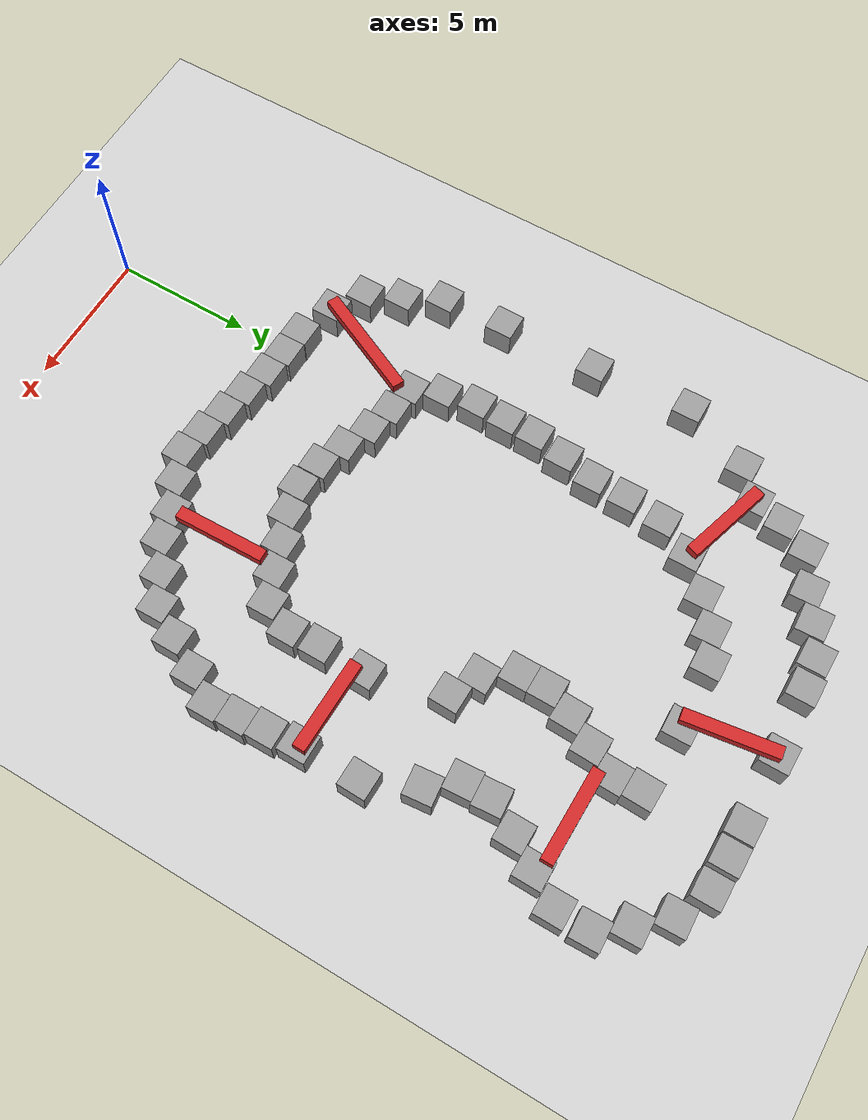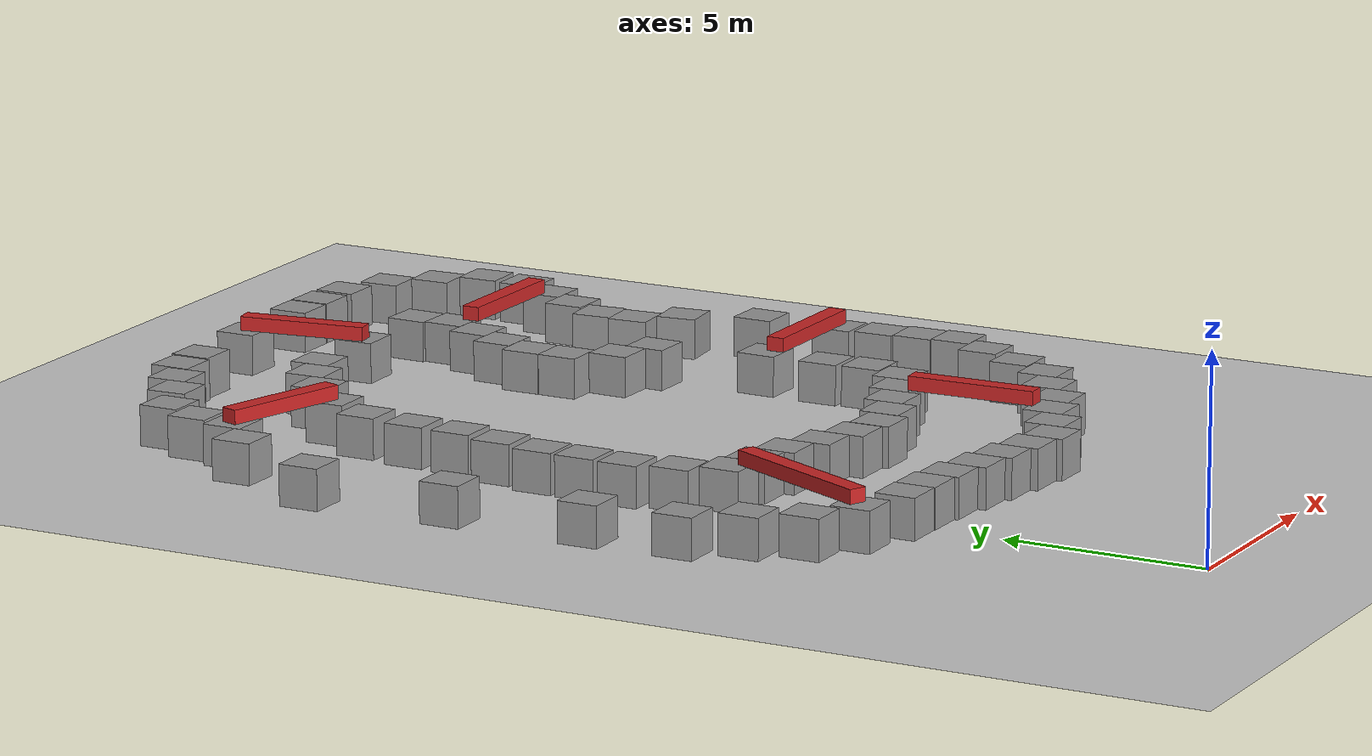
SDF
<sdf version="1.7">
 <world name="default">
  <model name="ground_plane">
   <static>1</static>
   <link name="link">
    <collision name="collision">
     <geometry><plane><normal>0 0 1</normal><size>100 100</size></plane></geometry>
     <surface><friction><ode><mu>100</mu><mu2>50</mu2></ode></friction></surface>
    </collision>
    <visual name="visual">
     <cast_shadows>0</cast_shadows>
     <geometry><plane><normal>0 0 1</normal><size>100 100</size></plane></geometry>
     <material>
      <script><uri>file://media/materials/scripts/gazebo.material</uri><name>Gazebo/Grey</name></script>
     </material>
    </visual>
   </link>
  </model>
  <light name="sun" type="directional">
   <pose>0 0 10 0 -0 0</pose>
   <diffuse>0.8 0.8 0.8 1</diffuse>
   <specular>0.2 0.2 0.2 1</specular>
   <attenuation>
    <range>1000</range>
    <constant>0.9</constant>
    <linear>0.01</linear>
    <quadratic>0.001</quadratic>
   </attenuation>
   <direction>-0.5 0.1 -0.9</direction>
   <spot><inner_angle>0</inner_angle><outer_angle>0</outer_angle><falloff>0</falloff></spot>
  </light>
  <gravity>0 0 -9.8</gravity>
  <magnetic_field>6e-06 2.3e-05 -4.2e-05</magnetic_field>
  <atmosphere type="adiabatic"/>
  <physics type="ode">
   <max_step_size>0.001</max_step_size>
   <real_time_factor>1</real_time_factor>
   <real_time_update_rate>1000</real_time_update_rate>
  </physics>
  <scene><ambient>0.4 0.4 0.4 1</ambient><background>0.7 0.7 0.7 1</background><shadows>1</shadows></scene>
  <audio><device>default</device></audio>
  <spherical_coordinates>
   <surface_model>EARTH_WGS84</surface_model>
   <latitude_deg>0</latitude_deg>
   <longitude_deg>0</longitude_deg>
   <elevation>0</elevation>
   <heading_deg>0</heading_deg>
  </spherical_coordinates>
  <model name="unit_box">
   <pose>-0.526604 7.20124 0.5 0 0 -0.00372</pose>
   <link name="link">
    <inertial>
     <mass>1</mass>
     <inertia>
      <ixx>0.166667</ixx>
      <ixy>0</ixy>
      <ixz>0</ixz>
      <iyy>0.166667</iyy>
      <iyz>0</iyz>
      <izz>0.166667</izz>
     </inertia>
    </inertial>
    <collision name="collision"><geometry><box><size>1 1 1</size></box></geometry></collision>
    <visual name="visual">
     <geometry><box><size>1 1 1</size></box></geometry>
     <material>
      <script><name>Gazebo/Grey</name><uri>file://media/materials/scripts/gazebo.material</uri></script>
     </material>
    </visual>
   </link>
  </model>
  <model name="unit_box_0">
   <pose>-0.443298 11.6969 0.5 0 0 -0.000523</pose>
   <link name="link">
    <inertial>
     <mass>1</mass>
     <inertia>
      <ixx>0.166667</ixx>
      <ixy>0</ixy>
      <ixz>0</ixz>
      <iyy>0.166667</iyy>
      <iyz>0</iyz>
      <izz>0.166667</izz>
     </inertia>
    </inertial>
    <collision name="collision"><geometry><box><size>1 1 1</size></box></geometry></collision>
    <visual name="visual">
     <geometry><box><size>1 1 1</size></box></geometry>
     <material>
      <script><name>Gazebo/Grey</name><uri>file://media/materials/scripts/gazebo.material</uri></script>
     </material>
    </visual>
   </link>
  </model>
  <model name="unit_box_1">
   <pose>0.473311 7.1762 0.499995 -1e-05 -0 -0.00372</pose>
   <link name="link">
    <inertial>
     <mass>1</mass>
     <inertia>
      <ixx>0.166667</ixx>
      <ixy>0</ixy>
      <ixz>0</ixz>
      <iyy>0.166667</iyy>
      <iyz>0</iyz>
      <izz>0.166667</izz>
     </inertia>
    </inertial>
    <collision name="collision"><geometry><box><size>1 1 1</size></box></geometry></collision>
    <visual name="visual">
     <geometry><box><size>1 1 1</size></box></geometry>
     <material>
      <script><name>Gazebo/Grey</name><uri>file://media/materials/scripts/gazebo.material</uri></script>
     </material>
    </visual>
   </link>
  </model>
  <model name="unit_box_2">
   <pose>1.47302 7.07448 0.499995 0 1e-05 -0.003884</pose>
   <link name="link">
    <inertial>
     <mass>1</mass>
     <inertia>
      <ixx>0.166667</ixx>
      <ixy>0</ixy>
      <ixz>0</ixz>
      <iyy>0.166667</iyy>
      <iyz>0</iyz>
      <izz>0.166667</izz>
     </inertia>
    </inertial>
    <collision name="collision"><geometry><box><size>1 1 1</size></box></geometry></collision>
    <visual name="visual">
     <geometry><box><size>1 1 1</size></box></geometry>
     <material>
      <script><name>Gazebo/Grey</name><uri>file://media/materials/scripts/gazebo.material</uri></script>
     </material>
    </visual>
   </link>
  </model>
  <model name="unit_box_3">
   <pose>2.4724 6.86705 0.499995 -0 1e-05 -0.003816</pose>
   <link name="link">
    <inertial>
     <mass>1</mass>
     <inertia>
      <ixx>0.166667</ixx>
      <ixy>0</ixy>
      <ixz>0</ixz>
      <iyy>0.166667</iyy>
      <iyz>0</iyz>
      <izz>0.166667</izz>
     </inertia>
    </inertial>
    <collision name="collision"><geometry><box><size>1 1 1</size></box></geometry></collision>
    <visual name="visual">
     <geometry><box><size>1 1 1</size></box></geometry>
     <material>
      <script><name>Gazebo/Grey</name><uri>file://media/materials/scripts/gazebo.material</uri></script>
     </material>
    </visual>
   </link>
  </model>
  <model name="unit_box_4">
   <pose>0.557502 11.5442 0.5 0 -0 0.000137</pose>
   <link name="link">
    <inertial>
     <mass>1</mass>
     <inertia>
      <ixx>0.166667</ixx>
      <ixy>0</ixy>
      <ixz>0</ixz>
      <iyy>0.166667</iyy>
      <iyz>0</iyz>
      <izz>0.166667</izz>
     </inertia>
    </inertial>
    <collision name="collision"><geometry><box><size>1 1 1</size></box></geometry></collision>
    <visual name="visual">
     <geometry><box><size>1 1 1</size></box></geometry>
     <material>
      <script><name>Gazebo/Grey</name><uri>file://media/materials/scripts/gazebo.material</uri></script>
     </material>
    </visual>
   </link>
  </model>
  <model name="unit_box_5">
   <pose>1.56131 11.2931 0.499995 0 -1e-05 -0.001514</pose>
   <link name="link">
    <inertial>
     <mass>1</mass>
     <inertia>
      <ixx>0.166667</ixx>
      <ixy>0</ixy>
      <ixz>0</ixz>
      <iyy>0.166667</iyy>
      <iyz>0</iyz>
      <izz>0.166667</izz>
     </inertia>
    </inertial>
    <collision name="collision"><geometry><box><size>1 1 1</size></box></geometry></collision>
    <visual name="visual">
     <geometry><box><size>1 1 1</size></box></geometry>
     <material>
      <script><name>Gazebo/Grey</name><uri>file://media/materials/scripts/gazebo.material</uri></script>
     </material>
    </visual>
   </link>
  </model>
  <model name="unit_box_6">
   <pose>2.56069 10.8846 0.499995 -0 -1e-05 -0.001517</pose>
   <link name="link">
    <inertial>
     <mass>1</mass>
     <inertia>
      <ixx>0.166667</ixx>
      <ixy>0</ixy>
      <ixz>0</ixz>
      <iyy>0.166667</iyy>
      <iyz>0</iyz>
      <izz>0.166667</izz>
     </inertia>
    </inertial>
    <collision name="collision"><geometry><box><size>1 1 1</size></box></geometry></collision>
    <visual name="visual">
     <geometry><box><size>1 1 1</size></box></geometry>
     <material>
      <script><name>Gazebo/Grey</name><uri>file://media/materials/scripts/gazebo.material</uri></script>
     </material>
    </visual>
   </link>
  </model>
  <model name="unit_box_7">
   <pose>3.4724 6.69284 0.5 -0 1e-06 -0.002959</pose>
   <link name="link">
    <inertial>
     <mass>1</mass>
     <inertia>
      <ixx>0.166667</ixx>
      <ixy>0</ixy>
      <ixz>0</ixz>
      <iyy>0.166667</iyy>
      <iyz>0</iyz>
      <izz>0.166667</izz>
     </inertia>
    </inertial>
    <collision name="collision"><geometry><box><size>1 1 1</size></box></geometry></collision>
    <visual name="visual">
     <geometry><box><size>1 1 1</size></box></geometry>
     <material>
      <script><name>Gazebo/Grey</name><uri>file://media/materials/scripts/gazebo.material</uri></script>
     </material>
    </visual>
   </link>
  </model>
  <model name="unit_box_8">
   <pose>3.56065 10.5336 0.499995 1e-05 -0 -0.001533</pose>
   <link name="link">
    <inertial>
     <mass>1</mass>
     <inertia>
      <ixx>0.166667</ixx>
      <ixy>0</ixy>
      <ixz>0</ixz>
      <iyy>0.166667</iyy>
      <iyz>0</iyz>
      <izz>0.166667</izz>
     </inertia>
    </inertial>
    <collision name="collision"><geometry><box><size>1 1 1</size></box></geometry></collision>
    <visual name="visual">
     <geometry><box><size>1 1 1</size></box></geometry>
     <material>
      <script><name>Gazebo/Grey</name><uri>file://media/materials/scripts/gazebo.material</uri></script>
     </material>
    </visual>
   </link>
  </model>
  <model name="unit_box_9">
   <pose>4.47191 6.50319 0.5 -0 -0 -0.002823</pose>
   <link name="link">
    <inertial>
     <mass>1</mass>
     <inertia>
      <ixx>0.166667</ixx>
      <ixy>0</ixy>
      <ixz>0</ixz>
      <iyy>0.166667</iyy>
      <iyz>0</iyz>
      <izz>0.166667</izz>
     </inertia>
    </inertial>
    <collision name="collision"><geometry><box><size>1 1 1</size></box></geometry></collision>
    <visual name="visual">
     <geometry><box><size>1 1 1</size></box></geometry>
     <material>
      <script><name>Gazebo/Grey</name><uri>file://media/materials/scripts/gazebo.material</uri></script>
     </material>
    </visual>
   </link>
  </model>
  <model name="unit_box_10">
   <pose>4.58383 10.3824 0.499995 0 -1e-05 0</pose>
   <link name="link">
    <inertial>
     <mass>1</mass>
     <inertia>
      <ixx>0.166667</ixx>
      <ixy>0</ixy>
      <ixz>0</ixz>
      <iyy>0.166667</iyy>
      <iyz>0</iyz>
      <izz>0.166667</izz>
     </inertia>
    </inertial>
    <collision name="collision"><geometry><box><size>1 1 1</size></box></geometry></collision>
    <visual name="visual">
     <geometry><box><size>1 1 1</size></box></geometry>
     <material>
      <script><name>Gazebo/Grey</name><uri>file://media/materials/scripts/gazebo.material</uri></script>
     </material>
    </visual>
   </link>
  </model>
  <model name="unit_box_11">
   <pose>5.47152 6.35499 0.5 -0 -0 -0.002771</pose>
   <link name="link">
    <inertial>
     <mass>1</mass>
     <inertia>
      <ixx>0.166667</ixx>
      <ixy>0</ixy>
      <ixz>0</ixz>
      <iyy>0.166667</iyy>
      <iyz>0</iyz>
      <izz>0.166667</izz>
     </inertia>
    </inertial>
    <collision name="collision"><geometry><box><size>1 1 1</size></box></geometry></collision>
    <visual name="visual">
     <geometry><box><size>1 1 1</size></box></geometry>
     <material>
      <script><name>Gazebo/Grey</name><uri>file://media/materials/scripts/gazebo.material</uri></script>
     </material>
    </visual>
   </link>
  </model>
  <model name="unit_box_12">
   <pose>6.4733 6.79545 0.5 0 -0 0.006562</pose>
   <link name="link">
    <inertial>
     <mass>1</mass>
     <inertia>
      <ixx>0.166667</ixx>
      <ixy>0</ixy>
      <ixz>0</ixz>
      <iyy>0.166667</iyy>
      <iyz>0</iyz>
      <izz>0.166667</izz>
     </inertia>
    </inertial>
    <collision name="collision"><geometry><box><size>1 1 1</size></box></geometry></collision>
    <visual name="visual">
     <geometry><box><size>1 1 1</size></box></geometry>
     <material>
      <script><name>Gazebo/Grey</name><uri>file://media/materials/scripts/gazebo.material</uri></script>
     </material>
    </visual>
   </link>
  </model>
  <model name="unit_box_13">
   <pose>7.47097 7.31149 0.499942 -4.9e-05 -2.1e-05 0.015315</pose>
   <link name="link">
    <inertial>
     <mass>1</mass>
     <inertia>
      <ixx>0.166667</ixx>
      <ixy>0</ixy>
      <ixz>0</ixz>
      <iyy>0.166667</iyy>
      <iyz>0</iyz>
      <izz>0.166667</izz>
     </inertia>
    </inertial>
    <collision name="collision"><geometry><box><size>1 1 1</size></box></geometry></collision>
    <visual name="visual">
     <geometry><box><size>1 1 1</size></box></geometry>
     <material>
      <script><name>Gazebo/Grey</name><uri>file://media/materials/scripts/gazebo.material</uri></script>
     </material>
    </visual>
   </link>
  </model>
  <model name="unit_box_14">
   <pose>5.59272 10.6388 0.499995 -1e-05 -0 0.007795</pose>
   <link name="link">
    <inertial>
     <mass>1</mass>
     <inertia>
      <ixx>0.166667</ixx>
      <ixy>0</ixy>
      <ixz>0</ixz>
      <iyy>0.166667</iyy>
      <iyz>0</iyz>
      <izz>0.166667</izz>
     </inertia>
    </inertial>
    <collision name="collision"><geometry><box><size>1 1 1</size></box></geometry></collision>
    <visual name="visual">
     <geometry><box><size>1 1 1</size></box></geometry>
     <material>
      <script><name>Gazebo/Grey</name><uri>file://media/materials/scripts/gazebo.material</uri></script>
     </material>
    </visual>
   </link>
  </model>
  <model name="unit_box_15">
   <pose>6.59032 11.0295 0.499995 0 1e-05 0.012888</pose>
   <link name="link">
    <inertial>
     <mass>1</mass>
     <inertia>
      <ixx>0.166667</ixx>
      <ixy>0</ixy>
      <ixz>0</ixz>
      <iyy>0.166667</iyy>
      <iyz>0</iyz>
      <izz>0.166667</izz>
     </inertia>
    </inertial>
    <collision name="collision"><geometry><box><size>1 1 1</size></box></geometry></collision>
    <visual name="visual">
     <geometry><box><size>1 1 1</size></box></geometry>
     <material>
      <script><name>Gazebo/Grey</name><uri>file://media/materials/scripts/gazebo.material</uri></script>
     </material>
    </visual>
   </link>
  </model>
  <model name="unit_box_16">
   <pose>7.58676 11.3877 0.499834 0.000162 -2.5e-05 0.01422</pose>
   <link name="link">
    <inertial>
     <mass>1</mass>
     <inertia>
      <ixx>0.166667</ixx>
      <ixy>0</ixy>
      <ixz>0</ixz>
      <iyy>0.166667</iyy>
      <iyz>0</iyz>
      <izz>0.166667</izz>
     </inertia>
    </inertial>
    <collision name="collision"><geometry><box><size>1 1 1</size></box></geometry></collision>
    <visual name="visual">
     <geometry><box><size>1 1 1</size></box></geometry>
     <material>
      <script><name>Gazebo/Grey</name><uri>file://media/materials/scripts/gazebo.material</uri></script>
     </material>
    </visual>
   </link>
  </model>
  <model name="unit_box_17">
   <pose>8.46684 7.61038 0.499995 1e-05 -0 0.01482</pose>
   <link name="link">
    <inertial>
     <mass>1</mass>
     <inertia>
      <ixx>0.166667</ixx>
      <ixy>0</ixy>
      <ixz>0</ixz>
      <iyy>0.166667</iyy>
      <iyz>0</iyz>
      <izz>0.166667</izz>
     </inertia>
    </inertial>
    <collision name="collision"><geometry><box><size>1 1 1</size></box></geometry></collision>
    <visual name="visual">
     <geometry><box><size>1 1 1</size></box></geometry>
     <material>
      <script><name>Gazebo/Grey</name><uri>file://media/materials/scripts/gazebo.material</uri></script>
     </material>
    </visual>
   </link>
  </model>
  <model name="unit_box_18">
   <pose>9.45707 8.28467 0.499995 1e-05 -0 0.017206</pose>
   <link name="link">
    <inertial>
     <mass>1</mass>
     <inertia>
      <ixx>0.166667</ixx>
      <ixy>0</ixy>
      <ixz>0</ixz>
      <iyy>0.166667</iyy>
      <iyz>0</iyz>
      <izz>0.166667</izz>
     </inertia>
    </inertial>
    <collision name="collision"><geometry><box><size>1 1 1</size></box></geometry></collision>
    <visual name="visual">
     <geometry><box><size>1 1 1</size></box></geometry>
     <material>
      <script><name>Gazebo/Grey</name><uri>file://media/materials/scripts/gazebo.material</uri></script>
     </material>
    </visual>
   </link>
  </model>
  <model name="unit_box_19">
   <pose>8.58109 11.8007 0.499995 -1e-05 -0 0.014428</pose>
   <link name="link">
    <inertial>
     <mass>1</mass>
     <inertia>
      <ixx>0.166667</ixx>
      <ixy>0</ixy>
      <ixz>0</ixz>
      <iyy>0.166667</iyy>
      <iyz>0</iyz>
      <izz>0.166667</izz>
     </inertia>
    </inertial>
    <collision name="collision"><geometry><box><size>1 1 1</size></box></geometry></collision>
    <visual name="visual">
     <geometry><box><size>1 1 1</size></box></geometry>
     <material>
      <script><name>Gazebo/Grey</name><uri>file://media/materials/scripts/gazebo.material</uri></script>
     </material>
    </visual>
   </link>
  </model>
  <model name="unit_box_20">
   <pose>10.4486 8.84699 0.499995 -1e-05 0 0.015731</pose>
   <link name="link">
    <inertial>
     <mass>1</mass>
     <inertia>
      <ixx>0.166667</ixx>
      <ixy>0</ixy>
      <ixz>0</ixz>
      <iyy>0.166667</iyy>
      <iyz>0</iyz>
      <izz>0.166667</izz>
     </inertia>
    </inertial>
    <collision name="collision"><geometry><box><size>1 1 1</size></box></geometry></collision>
    <visual name="visual">
     <geometry><box><size>1 1 1</size></box></geometry>
     <material>
      <script><name>Gazebo/Grey</name><uri>file://media/materials/scripts/gazebo.material</uri></script>
     </material>
    </visual>
   </link>
  </model>
  <model name="unit_box_21">
   <pose>9.0321 12.8398 0.499995 -1e-05 -0 1.7e-05</pose>
   <link name="link">
    <inertial>
     <mass>1</mass>
     <inertia>
      <ixx>0.166667</ixx>
      <ixy>0</ixy>
      <ixz>0</ixz>
      <iyy>0.166667</iyy>
      <iyz>0</iyz>
      <izz>0.166667</izz>
     </inertia>
    </inertial>
    <collision name="collision"><geometry><box><size>1 1 1</size></box></geometry></collision>
    <visual name="visual">
     <geometry><box><size>1 1 1</size></box></geometry>
     <material>
      <script><name>Gazebo/Grey</name><uri>file://media/materials/scripts/gazebo.material</uri></script>
     </material>
    </visual>
   </link>
  </model>
  <model name="unit_box_22">
   <pose>11.0664 9.87961 0.499995 -1e-05 -0 -3e-06</pose>
   <link name="link">
    <inertial>
     <mass>1</mass>
     <inertia>
      <ixx>0.166667</ixx>
      <ixy>0</ixy>
      <ixz>0</ixz>
      <iyy>0.166667</iyy>
      <iyz>0</iyz>
      <izz>0.166667</izz>
     </inertia>
    </inertial>
    <collision name="collision"><geometry><box><size>1 1 1</size></box></geometry></collision>
    <visual name="visual">
     <geometry><box><size>1 1 1</size></box></geometry>
     <material>
      <script><name>Gazebo/Grey</name><uri>file://media/materials/scripts/gazebo.material</uri></script>
     </material>
    </visual>
   </link>
  </model>
  <model name="unit_box_23">
   <pose>11.7095 11.0275 0.499995 0 -1e-05 0</pose>
   <link name="link">
    <inertial>
     <mass>1</mass>
     <inertia>
      <ixx>0.166667</ixx>
      <ixy>0</ixy>
      <ixz>0</ixz>
      <iyy>0.166667</iyy>
      <iyz>0</iyz>
      <izz>0.166667</izz>
     </inertia>
    </inertial>
    <collision name="collision"><geometry><box><size>1 1 1</size></box></geometry></collision>
    <visual name="visual">
     <geometry><box><size>1 1 1</size></box></geometry>
     <material>
      <script><name>Gazebo/Grey</name><uri>file://media/materials/scripts/gazebo.material</uri></script>
     </material>
    </visual>
   </link>
  </model>
  <model name="unit_box_24">
   <pose>12.3045 12.0441 0.499995 0 -1e-05 0.01059</pose>
   <link name="link">
    <inertial>
     <mass>1</mass>
     <inertia>
      <ixx>0.166667</ixx>
      <ixy>0</ixy>
      <ixz>0</ixz>
      <iyy>0.166667</iyy>
      <iyz>0</iyz>
      <izz>0.166667</izz>
     </inertia>
    </inertial>
    <collision name="collision"><geometry><box><size>1 1 1</size></box></geometry></collision>
    <visual name="visual">
     <geometry><box><size>1 1 1</size></box></geometry>
     <material>
      <script><name>Gazebo/Grey</name><uri>file://media/materials/scripts/gazebo.material</uri></script>
     </material>
    </visual>
   </link>
  </model>
  <model name="unit_box_25">
   <pose>8.97791 13.9722 0.499995 0 -1e-05 0</pose>
   <link name="link">
    <inertial>
     <mass>1</mass>
     <inertia>
      <ixx>0.166667</ixx>
      <ixy>0</ixy>
      <ixz>0</ixz>
      <iyy>0.166667</iyy>
      <iyz>0</iyz>
      <izz>0.166667</izz>
     </inertia>
    </inertial>
    <collision name="collision"><geometry><box><size>1 1 1</size></box></geometry></collision>
    <visual name="visual">
     <geometry><box><size>1 1 1</size></box></geometry>
     <material>
      <script><name>Gazebo/Grey</name><uri>file://media/materials/scripts/gazebo.material</uri></script>
     </material>
    </visual>
   </link>
  </model>
  <model name="unit_box_26">
   <pose>12.2214 13.0435 0.5 0 -0 0.010546</pose>
   <link name="link">
    <inertial>
     <mass>1</mass>
     <inertia>
      <ixx>0.166667</ixx>
      <ixy>0</ixy>
      <ixz>0</ixz>
      <iyy>0.166667</iyy>
      <iyz>0</iyz>
      <izz>0.166667</izz>
     </inertia>
    </inertial>
    <collision name="collision"><geometry><box><size>1 1 1</size></box></geometry></collision>
    <visual name="visual">
     <geometry><box><size>1 1 1</size></box></geometry>
     <material>
      <script><name>Gazebo/Grey</name><uri>file://media/materials/scripts/gazebo.material</uri></script>
     </material>
    </visual>
   </link>
  </model>
  <model name="unit_box_27">
   <pose>12.1184 14.0428 0.499995 0 -1e-05 0.010987</pose>
   <link name="link">
    <inertial>
     <mass>1</mass>
     <inertia>
      <ixx>0.166667</ixx>
      <ixy>0</ixy>
      <ixz>0</ixz>
      <iyy>0.166667</iyy>
      <iyz>0</iyz>
      <izz>0.166667</izz>
     </inertia>
    </inertial>
    <collision name="collision"><geometry><box><size>1 1 1</size></box></geometry></collision>
    <visual name="visual">
     <geometry><box><size>1 1 1</size></box></geometry>
     <material>
      <script><name>Gazebo/Grey</name><uri>file://media/materials/scripts/gazebo.material</uri></script>
     </material>
    </visual>
   </link>
  </model>
  <model name="unit_box_28">
   <pose>12.0032 15.1306 0.499998 4e-06 0 0.001433</pose>
   <link name="link">
    <inertial>
     <mass>1</mass>
     <inertia>
      <ixx>0.166667</ixx>
      <ixy>0</ixy>
      <ixz>0</ixz>
      <iyy>0.166667</iyy>
      <iyz>0</iyz>
      <izz>0.166667</izz>
     </inertia>
    </inertial>
    <collision name="collision"><geometry><box><size>1 1 1</size></box></geometry></collision>
    <visual name="visual">
     <geometry><box><size>1 1 1</size></box></geometry>
     <material>
      <script><name>Gazebo/Grey</name><uri>file://media/materials/scripts/gazebo.material</uri></script>
     </material>
    </visual>
   </link>
  </model>
  <model name="unit_box_29">
   <pose>12.0081 17.2916 0.499995 1e-05 -0 -0.024336</pose>
   <link name="link">
    <inertial>
     <mass>1</mass>
     <inertia>
      <ixx>0.166667</ixx>
      <ixy>0</ixy>
      <ixz>0</ixz>
      <iyy>0.166667</iyy>
      <iyz>0</iyz>
      <izz>0.166667</izz>
     </inertia>
    </inertial>
    <collision name="collision"><geometry><box><size>1 0.999996 1</size></box></geometry></collision>
    <visual name="visual">
     <geometry><box><size>1 0.999996 1</size></box></geometry>
     <material>
      <script><name>Gazebo/Grey</name><uri>file://media/materials/scripts/gazebo.material</uri></script>
     </material>
    </visual>
   </link>
  </model>
  <model name="unit_box_30">
   <pose>9.00415 15.636 0.499982 5e-06 -0 -0.027018</pose>
   <link name="link">
    <inertial>
     <mass>1</mass>
     <inertia>
      <ixx>0.166667</ixx>
      <ixy>0</ixy>
      <ixz>0</ixz>
      <iyy>0.166667</iyy>
      <iyz>0</iyz>
      <izz>0.166667</izz>
     </inertia>
    </inertial>
    <collision name="collision"><geometry><box><size>1 0.999999 1</size></box></geometry></collision>
    <visual name="visual">
     <geometry><box><size>1 0.999999 1</size></box></geometry>
     <material>
      <script><name>Gazebo/Grey</name><uri>file://media/materials/scripts/gazebo.material</uri></script>
     </material>
    </visual>
   </link>
  </model>
  <model name="unit_box_31">
   <pose>11.2269 19.05 0.5 0 -0 0.100627</pose>
   <link name="link">
    <inertial>
     <mass>1</mass>
     <inertia>
      <ixx>0.166667</ixx>
      <ixy>0</ixy>
      <ixz>0</ixz>
      <iyy>0.166667</iyy>
      <iyz>0</iyz>
      <izz>0.166667</izz>
     </inertia>
    </inertial>
    <collision name="collision"><geometry><box><size>1 1 1</size></box></geometry></collision>
    <visual name="visual">
     <geometry><box><size>1 1 1</size></box></geometry>
     <material>
      <script><name>Gazebo/Grey</name><uri>file://media/materials/scripts/gazebo.material</uri></script>
     </material>
    </visual>
   </link>
  </model>
  <model name="unit_box_32">
   <pose>8.29846 18.3019 0.499995 0 -1e-05 -0.024164</pose>
   <link name="link">
    <inertial>
     <mass>1</mass>
     <inertia>
      <ixx>0.166667</ixx>
      <ixy>0</ixy>
      <ixz>0</ixz>
      <iyy>0.166667</iyy>
      <iyz>0</iyz>
      <izz>0.166667</izz>
     </inertia>
    </inertial>
    <collision name="collision"><geometry><box><size>1 1 1</size></box></geometry></collision>
    <visual name="visual">
     <geometry><box><size>1 1 1</size></box></geometry>
     <material>
      <script><name>Gazebo/Grey</name><uri>file://media/materials/scripts/gazebo.material</uri></script>
     </material>
    </visual>
   </link>
  </model>
  <model name="unit_box_33">
   <pose>7.30964 18.7818 0.499995 0 1e-05 -0.024113</pose>
   <link name="link">
    <inertial>
     <mass>1</mass>
     <inertia>
      <ixx>0.166667</ixx>
      <ixy>0</ixy>
      <ixz>0</ixz>
      <iyy>0.166667</iyy>
      <iyz>0</iyz>
      <izz>0.166667</izz>
     </inertia>
    </inertial>
    <collision name="collision"><geometry><box><size>1 1 1</size></box></geometry></collision>
    <visual name="visual">
     <geometry><box><size>1 1 1</size></box></geometry>
     <material>
      <script><name>Gazebo/Grey</name><uri>file://media/materials/scripts/gazebo.material</uri></script>
     </material>
    </visual>
   </link>
  </model>
  <model name="unit_box_34">
   <pose>6.6108 19.8024 0.499995 0 -1e-05 -0.003081</pose>
   <link name="link">
    <inertial>
     <mass>1</mass>
     <inertia>
      <ixx>0.166667</ixx>
      <ixy>0</ixy>
      <ixz>0</ixz>
      <iyy>0.166667</iyy>
      <iyz>0</iyz>
      <izz>0.166667</izz>
     </inertia>
    </inertial>
    <collision name="collision"><geometry><box><size>1 1 1</size></box></geometry></collision>
    <visual name="visual">
     <geometry><box><size>1 1 1</size></box></geometry>
     <material>
      <script><name>Gazebo/Grey</name><uri>file://media/materials/scripts/gazebo.material</uri></script>
     </material>
    </visual>
   </link>
  </model>
  <model name="unit_box_35">
   <pose>10.4664 19.9942 0.5 0 -0 0.068452</pose>
   <link name="link">
    <inertial>
     <mass>1</mass>
     <inertia>
      <ixx>0.166667</ixx>
      <ixy>0</ixy>
      <ixz>0</ixz>
      <iyy>0.166667</iyy>
      <iyz>0</iyz>
      <izz>0.166667</izz>
     </inertia>
    </inertial>
    <collision name="collision"><geometry><box><size>1 1 1</size></box></geometry></collision>
    <visual name="visual">
     <geometry><box><size>1 1 1</size></box></geometry>
     <material>
      <script><name>Gazebo/Grey</name><uri>file://media/materials/scripts/gazebo.material</uri></script>
     </material>
    </visual>
   </link>
  </model>
  <model name="unit_box_36">
   <pose>10.4725 20.9969 0.5 0 -0 0.068451</pose>
   <link name="link">
    <inertial>
     <mass>1</mass>
     <inertia>
      <ixx>0.166667</ixx>
      <ixy>0</ixy>
      <ixz>0</ixz>
      <iyy>0.166667</iyy>
      <iyz>0</iyz>
      <izz>0.166667</izz>
     </inertia>
    </inertial>
    <collision name="collision"><geometry><box><size>1 1 1</size></box></geometry></collision>
    <visual name="visual">
     <geometry><box><size>1 1 1</size></box></geometry>
     <material>
      <script><name>Gazebo/Grey</name><uri>file://media/materials/scripts/gazebo.material</uri></script>
     </material>
    </visual>
   </link>
  </model>
  <model name="unit_box_37">
   <pose>6.60546 20.8025 0.5 0 -0 -0.003129</pose>
   <link name="link">
    <inertial>
     <mass>1</mass>
     <inertia>
      <ixx>0.166667</ixx>
      <ixy>0</ixy>
      <ixz>0</ixz>
      <iyy>0.166667</iyy>
      <iyz>0</iyz>
      <izz>0.166667</izz>
     </inertia>
    </inertial>
    <collision name="collision"><geometry><box><size>1 1 1</size></box></geometry></collision>
    <visual name="visual">
     <geometry><box><size>1 1 1</size></box></geometry>
     <material>
      <script><name>Gazebo/Grey</name><uri>file://media/materials/scripts/gazebo.material</uri></script>
     </material>
    </visual>
   </link>
  </model>
  <model name="unit_box_38">
   <pose>11.0611 22.0712 0.49998 7e-06 -2e-06 -0.009984</pose>
   <link name="link">
    <inertial>
     <mass>1</mass>
     <inertia>
      <ixx>0.166667</ixx>
      <ixy>0</ixy>
      <ixz>0</ixz>
      <iyy>0.166667</iyy>
      <iyz>0</iyz>
      <izz>0.166667</izz>
     </inertia>
    </inertial>
    <collision name="collision"><geometry><box><size>1 1 1</size></box></geometry></collision>
    <visual name="visual">
     <geometry><box><size>1 1 1</size></box></geometry>
     <material>
      <script><name>Gazebo/Grey</name><uri>file://media/materials/scripts/gazebo.material</uri></script>
     </material>
    </visual>
   </link>
  </model>
  <model name="unit_box_39">
   <pose>11.7065 23.0653 0.5 0 0 -0.008951</pose>
   <link name="link">
    <inertial>
     <mass>1</mass>
     <inertia>
      <ixx>0.166667</ixx>
      <ixy>0</ixy>
      <ixz>0</ixz>
      <iyy>0.166667</iyy>
      <iyz>0</iyz>
      <izz>0.166667</izz>
     </inertia>
    </inertial>
    <collision name="collision"><geometry><box><size>1 1 1</size></box></geometry></collision>
    <visual name="visual">
     <geometry><box><size>1 1 1</size></box></geometry>
     <material>
      <script><name>Gazebo/Grey</name><uri>file://media/materials/scripts/gazebo.material</uri></script>
     </material>
    </visual>
   </link>
  </model>
  <model name="unit_box_40">
   <pose>6.99695 21.8048 0.499995 0 -1e-05 -0.032784</pose>
   <link name="link">
    <inertial>
     <mass>1</mass>
     <inertia>
      <ixx>0.166667</ixx>
      <ixy>0</ixy>
      <ixz>0</ixz>
      <iyy>0.166667</iyy>
      <iyz>0</iyz>
      <izz>0.166667</izz>
     </inertia>
    </inertial>
    <collision name="collision"><geometry><box><size>1 1 1</size></box></geometry></collision>
    <visual name="visual">
     <geometry><box><size>1 1 1</size></box></geometry>
     <material>
      <script><name>Gazebo/Grey</name><uri>file://media/materials/scripts/gazebo.material</uri></script>
     </material>
    </visual>
   </link>
  </model>
  <model name="unit_box_41">
   <pose>7.54915 22.7874 0.499995 0 -1e-05 -0.032706</pose>
   <link name="link">
    <inertial>
     <mass>1</mass>
     <inertia>
      <ixx>0.166667</ixx>
      <ixy>0</ixy>
      <ixz>0</ixz>
      <iyy>0.166667</iyy>
      <iyz>0</iyz>
      <izz>0.166667</izz>
     </inertia>
    </inertial>
    <collision name="collision"><geometry><box><size>1 1 1</size></box></geometry></collision>
    <visual name="visual">
     <geometry><box><size>1 1 1</size></box></geometry>
     <material>
      <script><name>Gazebo/Grey</name><uri>file://media/materials/scripts/gazebo.material</uri></script>
     </material>
    </visual>
   </link>
  </model>
  <model name="unit_box_42">
   <pose>12.3435 24.0958 0.499995 0 -1e-05 0</pose>
   <link name="link">
    <inertial>
     <mass>1</mass>
     <inertia>
      <ixx>0.166667</ixx>
      <ixy>0</ixy>
      <ixz>0</ixz>
      <iyy>0.166667</iyy>
      <iyz>0</iyz>
      <izz>0.166667</izz>
     </inertia>
    </inertial>
    <collision name="collision"><geometry><box><size>1 1 1</size></box></geometry></collision>
    <visual name="visual">
     <geometry><box><size>1 1 1</size></box></geometry>
     <material>
      <script><name>Gazebo/Grey</name><uri>file://media/materials/scripts/gazebo.material</uri></script>
     </material>
    </visual>
   </link>
  </model>
  <model name="unit_box_43">
   <pose>8.05112 23.775 0.5 0 0 -0.030671</pose>
   <link name="link">
    <inertial>
     <mass>1</mass>
     <inertia>
      <ixx>0.166667</ixx>
      <ixy>0</ixy>
      <ixz>0</ixz>
      <iyy>0.166667</iyy>
      <iyz>0</iyz>
      <izz>0.166667</izz>
     </inertia>
    </inertial>
    <collision name="collision"><geometry><box><size>1 1 1</size></box></geometry></collision>
    <visual name="visual">
     <geometry><box><size>1 1 1</size></box></geometry>
     <material>
      <script><name>Gazebo/Grey</name><uri>file://media/materials/scripts/gazebo.material</uri></script>
     </material>
    </visual>
   </link>
  </model>
  <model name="unit_box_44">
   <pose>12.391 25.2839 0.499995 0 1e-05 0.03194</pose>
   <link name="link">
    <inertial>
     <mass>1</mass>
     <inertia>
      <ixx>0.166667</ixx>
      <ixy>0</ixy>
      <ixz>0</ixz>
      <iyy>0.166667</iyy>
      <iyz>0</iyz>
      <izz>0.166667</izz>
     </inertia>
    </inertial>
    <collision name="collision"><geometry><box><size>1 1 1</size></box></geometry></collision>
    <visual name="visual">
     <geometry><box><size>1 1 1</size></box></geometry>
     <material>
      <script><name>Gazebo/Grey</name><uri>file://media/materials/scripts/gazebo.material</uri></script>
     </material>
    </visual>
   </link>
  </model>
  <model name="unit_box_45">
   <pose>7.99029 24.7773 0.499992 0 -1e-06 -0.030672</pose>
   <link name="link">
    <inertial>
     <mass>1</mass>
     <inertia>
      <ixx>0.166667</ixx>
      <ixy>0</ixy>
      <ixz>0</ixz>
      <iyy>0.166667</iyy>
      <iyz>0</iyz>
      <izz>0.166667</izz>
     </inertia>
    </inertial>
    <collision name="collision"><geometry><box><size>1 1 1</size></box></geometry></collision>
    <visual name="visual">
     <geometry><box><size>1 1 1</size></box></geometry>
     <material>
      <script><name>Gazebo/Grey</name><uri>file://media/materials/scripts/gazebo.material</uri></script>
     </material>
    </visual>
   </link>
  </model>
  <model name="unit_box_46">
   <pose>11.6614 26.2617 0.499995 -0 1e-05 0.031058</pose>
   <link name="link">
    <inertial>
     <mass>1</mass>
     <inertia>
      <ixx>0.166667</ixx>
      <ixy>0</ixy>
      <ixz>0</ixz>
      <iyy>0.166667</iyy>
      <iyz>0</iyz>
      <izz>0.166667</izz>
     </inertia>
    </inertial>
    <collision name="collision"><geometry><box><size>1 1 1</size></box></geometry></collision>
    <visual name="visual">
     <geometry><box><size>1 1 1</size></box></geometry>
     <material>
      <script><name>Gazebo/Grey</name><uri>file://media/materials/scripts/gazebo.material</uri></script>
     </material>
    </visual>
   </link>
  </model>
  <model name="unit_box_47">
   <pose>10.8073 27.2358 0.499995 -1e-05 -0 0.030886</pose>
   <link name="link">
    <inertial>
     <mass>1</mass>
     <inertia>
      <ixx>0.166667</ixx>
      <ixy>0</ixy>
      <ixz>0</ixz>
      <iyy>0.166667</iyy>
      <iyz>0</iyz>
      <izz>0.166667</izz>
     </inertia>
    </inertial>
    <collision name="collision"><geometry><box><size>1 1 1</size></box></geometry></collision>
    <visual name="visual">
     <geometry><box><size>1 1 1</size></box></geometry>
     <material>
      <script><name>Gazebo/Grey</name><uri>file://media/materials/scripts/gazebo.material</uri></script>
     </material>
    </visual>
   </link>
  </model>
  <model name="unit_box_48">
   <pose>9.57849 27.7816 0.499995 0 -1e-05 0</pose>
   <link name="link">
    <inertial>
     <mass>1</mass>
     <inertia>
      <ixx>0.166667</ixx>
      <ixy>0</ixy>
      <ixz>0</ixz>
      <iyy>0.166667</iyy>
      <iyz>0</iyz>
      <izz>0.166667</izz>
     </inertia>
    </inertial>
    <collision name="collision"><geometry><box><size>1 1 1</size></box></geometry></collision>
    <visual name="visual">
     <geometry><box><size>1 1 1</size></box></geometry>
     <material>
      <script><name>Gazebo/Grey</name><uri>file://media/materials/scripts/gazebo.material</uri></script>
     </material>
    </visual>
   </link>
  </model>
  <model name="unit_box_49">
   <pose>8.44638 27.8261 0.499995 0 -1e-05 0</pose>
   <link name="link">
    <inertial>
     <mass>1</mass>
     <inertia>
      <ixx>0.166667</ixx>
      <ixy>0</ixy>
      <ixz>0</ixz>
      <iyy>0.166667</iyy>
      <iyz>0</iyz>
      <izz>0.166667</izz>
     </inertia>
    </inertial>
    <collision name="collision"><geometry><box><size>1 1 1</size></box></geometry></collision>
    <visual name="visual">
     <geometry><box><size>1 1 1</size></box></geometry>
     <material>
      <script><name>Gazebo/Grey</name><uri>file://media/materials/scripts/gazebo.material</uri></script>
     </material>
    </visual>
   </link>
  </model>
  <model name="unit_box_50">
   <pose>4.91935 27.8257 0.499997 6e-06 0 -0.001145</pose>
   <link name="link">
    <inertial>
     <mass>1</mass>
     <inertia>
      <ixx>0.166667</ixx>
      <ixy>0</ixy>
      <ixz>0</ixz>
      <iyy>0.166667</iyy>
      <iyz>0</iyz>
      <izz>0.166667</izz>
     </inertia>
    </inertial>
    <collision name="collision"><geometry><box><size>0.999999 1 1</size></box></geometry></collision>
    <visual name="visual">
     <geometry><box><size>0.999999 1 1</size></box></geometry>
     <material>
      <script><name>Gazebo/Grey</name><uri>file://media/materials/scripts/gazebo.material</uri></script>
     </material>
    </visual>
   </link>
  </model>
  <model name="unit_box_51">
   <pose>7.39771 27.8228 0.499995 0 -1e-05 0</pose>
   <link name="link">
    <inertial>
     <mass>1</mass>
     <inertia>
      <ixx>0.166667</ixx>
      <ixy>0</ixy>
      <ixz>0</ixz>
      <iyy>0.166667</iyy>
      <iyz>0</iyz>
      <izz>0.166667</izz>
     </inertia>
    </inertial>
    <collision name="collision"><geometry><box><size>1 1 1</size></box></geometry></collision>
    <visual name="visual">
     <geometry><box><size>1 1 1</size></box></geometry>
     <material>
      <script><name>Gazebo/Grey</name><uri>file://media/materials/scripts/gazebo.material</uri></script>
     </material>
    </visual>
   </link>
  </model>
  <model name="unit_box_52">
   <pose>5.59188 24.8935 0.499991 -1e-06 1e-06 0.016913</pose>
   <link name="link">
    <inertial>
     <mass>1</mass>
     <inertia>
      <ixx>0.166667</ixx>
      <ixy>0</ixy>
      <ixz>0</ixz>
      <iyy>0.166667</iyy>
      <iyz>0</iyz>
      <izz>0.166667</izz>
     </inertia>
    </inertial>
    <collision name="collision"><geometry><box><size>1 1 1</size></box></geometry></collision>
    <visual name="visual">
     <geometry><box><size>1 1 1</size></box></geometry>
     <material>
      <script><name>Gazebo/Grey</name><uri>file://media/materials/scripts/gazebo.material</uri></script>
     </material>
    </visual>
   </link>
  </model>
  <model name="unit_box_53">
   <pose>3.30066 24.7514 0.5 0 -0 0.021486</pose>
   <link name="link">
    <inertial>
     <mass>1</mass>
     <inertia>
      <ixx>0.166667</ixx>
      <ixy>0</ixy>
      <ixz>0</ixz>
      <iyy>0.166667</iyy>
      <iyz>0</iyz>
      <izz>0.166667</izz>
     </inertia>
    </inertial>
    <collision name="collision"><geometry><box><size>1 1 1</size></box></geometry></collision>
    <visual name="visual">
     <geometry><box><size>1 1 1</size></box></geometry>
     <material>
      <script><name>Gazebo/Grey</name><uri>file://media/materials/scripts/gazebo.material</uri></script>
     </material>
    </visual>
   </link>
  </model>
  <model name="unit_box_54">
   <pose>2.30913 24.3076 0.499995 -1e-05 -0 0.031693</pose>
   <link name="link">
    <inertial>
     <mass>1</mass>
     <inertia>
      <ixx>0.166667</ixx>
      <ixy>0</ixy>
      <ixz>0</ixz>
      <iyy>0.166667</iyy>
      <iyz>0</iyz>
      <izz>0.166667</izz>
     </inertia>
    </inertial>
    <collision name="collision"><geometry><box><size>1 1 1</size></box></geometry></collision>
    <visual name="visual">
     <geometry><box><size>1 1 1</size></box></geometry>
     <material>
      <script><name>Gazebo/Grey</name><uri>file://media/materials/scripts/gazebo.material</uri></script>
     </material>
    </visual>
   </link>
  </model>
  <model name="unit_box_55">
   <pose>1.33211 23.5789 0.499995 -1e-05 -0 0.033791</pose>
   <link name="link">
    <inertial>
     <mass>1</mass>
     <inertia>
      <ixx>0.166667</ixx>
      <ixy>0</ixy>
      <ixz>0</ixz>
      <iyy>0.166667</iyy>
      <iyz>0</iyz>
      <izz>0.166667</izz>
     </inertia>
    </inertial>
    <collision name="collision"><geometry><box><size>1 1 1</size></box></geometry></collision>
    <visual name="visual">
     <geometry><box><size>1 1 1</size></box></geometry>
     <material>
      <script><name>Gazebo/Grey</name><uri>file://media/materials/scripts/gazebo.material</uri></script>
     </material>
    </visual>
   </link>
  </model>
  <model name="unit_box_56">
   <pose>2.56469 27.6472 0.499995 0 -1e-05 0</pose>
   <link name="link">
    <inertial>
     <mass>1</mass>
     <inertia>
      <ixx>0.166667</ixx>
      <ixy>0</ixy>
      <ixz>0</ixz>
      <iyy>0.166667</iyy>
      <iyz>0</iyz>
      <izz>0.166667</izz>
     </inertia>
    </inertial>
    <collision name="collision"><geometry><box><size>1 1 1</size></box></geometry></collision>
    <visual name="visual">
     <geometry><box><size>1 1 1</size></box></geometry>
     <material>
      <script><name>Gazebo/Grey</name><uri>file://media/materials/scripts/gazebo.material</uri></script>
     </material>
    </visual>
   </link>
  </model>
  <model name="unit_box_57">
   <pose>1.49299 27.5538 0.499995 0 -1e-05 0</pose>
   <link name="link">
    <inertial>
     <mass>1</mass>
     <inertia>
      <ixx>0.166667</ixx>
      <ixy>0</ixy>
      <ixz>0</ixz>
      <iyy>0.166667</iyy>
      <iyz>0</iyz>
      <izz>0.166667</izz>
     </inertia>
    </inertial>
    <collision name="collision"><geometry><box><size>1 1 1</size></box></geometry></collision>
    <visual name="visual">
     <geometry><box><size>1 1 1</size></box></geometry>
     <material>
      <script><name>Gazebo/Grey</name><uri>file://media/materials/scripts/gazebo.material</uri></script>
     </material>
    </visual>
   </link>
  </model>
  <model name="unit_box_58">
   <pose>0.453125 27.0163 0.5 0 -0 0.043039</pose>
   <link name="link">
    <inertial>
     <mass>1</mass>
     <inertia>
      <ixx>0.166667</ixx>
      <ixy>0</ixy>
      <ixz>0</ixz>
      <iyy>0.166667</iyy>
      <iyz>0</iyz>
      <izz>0.166667</izz>
     </inertia>
    </inertial>
    <collision name="collision"><geometry><box><size>1 1 1</size></box></geometry></collision>
    <visual name="visual">
     <geometry><box><size>1 1 1</size></box></geometry>
     <material>
      <script><name>Gazebo/Grey</name><uri>file://media/materials/scripts/gazebo.material</uri></script>
     </material>
    </visual>
   </link>
  </model>
  <model name="unit_box_59">
   <pose>-0.522531 26.4135 0.499995 0 1e-05 0.043043</pose>
   <link name="link">
    <inertial>
     <mass>1</mass>
     <inertia>
      <ixx>0.166667</ixx>
      <ixy>0</ixy>
      <ixz>0</ixz>
      <iyy>0.166667</iyy>
      <iyz>0</iyz>
      <izz>0.166667</izz>
     </inertia>
    </inertial>
    <collision name="collision"><geometry><box><size>1 1 1</size></box></geometry></collision>
    <visual name="visual">
     <geometry><box><size>1 1 1</size></box></geometry>
     <material>
      <script><name>Gazebo/Grey</name><uri>file://media/materials/scripts/gazebo.material</uri></script>
     </material>
    </visual>
   </link>
  </model>
  <model name="unit_box_60">
   <pose>-1.77889 25.8196 0.499995 0 -1e-05 0</pose>
   <link name="link">
    <inertial>
     <mass>1</mass>
     <inertia>
      <ixx>0.166667</ixx>
      <ixy>0</ixy>
      <ixz>0</ixz>
      <iyy>0.166667</iyy>
      <iyz>0</iyz>
      <izz>0.166667</izz>
     </inertia>
    </inertial>
    <collision name="collision"><geometry><box><size>1 1 1</size></box></geometry></collision>
    <visual name="visual">
     <geometry><box><size>1 1 1</size></box></geometry>
     <material>
      <script><name>Gazebo/Grey</name><uri>file://media/materials/scripts/gazebo.material</uri></script>
     </material>
    </visual>
   </link>
  </model>
  <model name="unit_box_61">
   <pose>-2.28487 24.7366 0.499995 0 -1e-05 0</pose>
   <link name="link">
    <inertial>
     <mass>1</mass>
     <inertia>
      <ixx>0.166667</ixx>
      <ixy>0</ixy>
      <ixz>0</ixz>
      <iyy>0.166667</iyy>
      <iyz>0</iyz>
      <izz>0.166667</izz>
     </inertia>
    </inertial>
    <collision name="collision"><geometry><box><size>1 1 1</size></box></geometry></collision>
    <visual name="visual">
     <geometry><box><size>1 1 1</size></box></geometry>
     <material>
      <script><name>Gazebo/Grey</name><uri>file://media/materials/scripts/gazebo.material</uri></script>
     </material>
    </visual>
   </link>
  </model>
  <model name="unit_box_62">
   <pose>-2.54114 23.6088 0.499964 -1e-05 -1e-06 -0.004934</pose>
   <link name="link">
    <inertial>
     <mass>1</mass>
     <inertia>
      <ixx>0.166667</ixx>
      <ixy>0</ixy>
      <ixz>0</ixz>
      <iyy>0.166667</iyy>
      <iyz>0</iyz>
      <izz>0.166667</izz>
     </inertia>
    </inertial>
    <collision name="collision"><geometry><box><size>1 1 1</size></box></geometry></collision>
    <visual name="visual">
     <geometry><box><size>1 1 1</size></box></geometry>
     <material>
      <script><name>Gazebo/Grey</name><uri>file://media/materials/scripts/gazebo.material</uri></script>
     </material>
    </visual>
   </link>
  </model>
  <model name="unit_box_63">
   <pose>-0.908237 12.7329 0.499995 0 -1e-05 0</pose>
   <link name="link">
    <inertial>
     <mass>1</mass>
     <inertia>
      <ixx>0.166667</ixx>
      <ixy>0</ixy>
      <ixz>0</ixz>
      <iyy>0.166667</iyy>
      <iyz>0</iyz>
      <izz>0.166667</izz>
     </inertia>
    </inertial>
    <collision name="collision"><geometry><box><size>1 1 1</size></box></geometry></collision>
    <visual name="visual">
     <geometry><box><size>1 1 1</size></box></geometry>
     <material>
      <script><name>Gazebo/Grey</name><uri>file://media/materials/scripts/gazebo.material</uri></script>
     </material>
    </visual>
   </link>
  </model>
  <model name="unit_box_64">
   <pose>-1.92328 7.62431 0.5 0 1e-06 -7.2e-05</pose>
   <link name="link">
    <inertial>
     <mass>1</mass>
     <inertia>
      <ixx>0.166667</ixx>
      <ixy>0</ixy>
      <ixz>0</ixz>
      <iyy>0.166667</iyy>
      <iyz>0</iyz>
      <izz>0.166667</izz>
     </inertia>
    </inertial>
    <collision name="collision"><geometry><box><size>1 1 1</size></box></geometry></collision>
    <visual name="visual">
     <geometry><box><size>1 1 1</size></box></geometry>
     <material>
      <script><name>Gazebo/Grey</name><uri>file://media/materials/scripts/gazebo.material</uri></script>
     </material>
    </visual>
   </link>
  </model>
  <model name="unit_box_65">
   <pose>-3.02283 8.33383 0.499995 0 -1e-05 0</pose>
   <link name="link">
    <inertial>
     <mass>1</mass>
     <inertia>
      <ixx>0.166667</ixx>
      <ixy>0</ixy>
      <ixz>0</ixz>
      <iyy>0.166667</iyy>
      <iyz>0</iyz>
      <izz>0.166667</izz>
     </inertia>
    </inertial>
    <collision name="collision"><geometry><box><size>1 1 1</size></box></geometry></collision>
    <visual name="visual">
     <geometry><box><size>1 1 1</size></box></geometry>
     <material>
      <script><name>Gazebo/Grey</name><uri>file://media/materials/scripts/gazebo.material</uri></script>
     </material>
    </visual>
   </link>
  </model>
  <model name="unit_box_66">
   <pose>-3.58695 9.5608 0.499995 0 -1e-05 0</pose>
   <link name="link">
    <inertial>
     <mass>1</mass>
     <inertia>
      <ixx>0.166667</ixx>
      <ixy>0</ixy>
      <ixz>0</ixz>
      <iyy>0.166667</iyy>
      <iyz>0</iyz>
      <izz>0.166667</izz>
     </inertia>
    </inertial>
    <collision name="collision"><geometry><box><size>1 1 1</size></box></geometry></collision>
    <visual name="visual">
     <geometry><box><size>1 1 1</size></box></geometry>
     <material>
      <script><name>Gazebo/Grey</name><uri>file://media/materials/scripts/gazebo.material</uri></script>
     </material>
    </visual>
   </link>
  </model>
  <model name="unit_box_67">
   <pose>-4.25429 10.87 0.499995 0 -1e-05 0</pose>
   <link name="link">
    <inertial>
     <mass>1</mass>
     <inertia>
      <ixx>0.166667</ixx>
      <ixy>0</ixy>
      <ixz>0</ixz>
      <iyy>0.166667</iyy>
      <iyz>0</iyz>
      <izz>0.166667</izz>
     </inertia>
    </inertial>
    <collision name="collision"><geometry><box><size>1 1 1</size></box></geometry></collision>
    <visual name="visual">
     <geometry><box><size>1 1 1</size></box></geometry>
     <material>
      <script><name>Gazebo/Grey</name><uri>file://media/materials/scripts/gazebo.material</uri></script>
     </material>
    </visual>
   </link>
  </model>
  <model name="unit_box_68">
   <pose>-1.13031 13.9512 0.499995 0 -1e-05 0</pose>
   <link name="link">
    <inertial>
     <mass>1</mass>
     <inertia>
      <ixx>0.166667</ixx>
      <ixy>0</ixy>
      <ixz>0</ixz>
      <iyy>0.166667</iyy>
      <iyz>0</iyz>
      <izz>0.166667</izz>
     </inertia>
    </inertial>
    <collision name="collision"><geometry><box><size>1 1 1</size></box></geometry></collision>
    <visual name="visual">
     <geometry><box><size>1 1 1</size></box></geometry>
     <material>
      <script><name>Gazebo/Grey</name><uri>file://media/materials/scripts/gazebo.material</uri></script>
     </material>
    </visual>
   </link>
  </model>
  <model name="unit_box_69">
   <pose>-1.08414 15.0957 0.499995 0 -1e-05 0</pose>
   <link name="link">
    <inertial>
     <mass>1</mass>
     <inertia>
      <ixx>0.166667</ixx>
      <ixy>0</ixy>
      <ixz>0</ixz>
      <iyy>0.166667</iyy>
      <iyz>0</iyz>
      <izz>0.166667</izz>
     </inertia>
    </inertial>
    <collision name="collision"><geometry><box><size>1 1 1</size></box></geometry></collision>
    <visual name="visual">
     <geometry><box><size>1 1 1</size></box></geometry>
     <material>
      <script><name>Gazebo/Grey</name><uri>file://media/materials/scripts/gazebo.material</uri></script>
     </material>
    </visual>
   </link>
  </model>
  <model name="unit_box_70">
   <pose>0.310886 22.5602 0.5 -2e-06 -3e-06 0.008293</pose>
   <link name="link">
    <inertial>
     <mass>1</mass>
     <inertia>
      <ixx>0.166667</ixx>
      <ixy>0</ixy>
      <ixz>0</ixz>
      <iyy>0.166667</iyy>
      <iyz>0</iyz>
      <izz>0.166667</izz>
     </inertia>
    </inertial>
    <collision name="collision"><geometry><box><size>1 1 1</size></box></geometry></collision>
    <visual name="visual">
     <geometry><box><size>1 1 1</size></box></geometry>
     <material>
      <script><name>Gazebo/Grey</name><uri>file://media/materials/scripts/gazebo.material</uri></script>
     </material>
    </visual>
   </link>
  </model>
  <model name="unit_box_71">
   <pose>-0.34897 21.3192 0.499995 -0 1e-05 -0.005315</pose>
   <link name="link">
    <inertial>
     <mass>1</mass>
     <inertia>
      <ixx>0.166667</ixx>
      <ixy>0</ixy>
      <ixz>0</ixz>
      <iyy>0.166667</iyy>
      <iyz>0</iyz>
      <izz>0.166667</izz>
     </inertia>
    </inertial>
    <collision name="collision"><geometry><box><size>1 1 1</size></box></geometry></collision>
    <visual name="visual">
     <geometry><box><size>1 1 1</size></box></geometry>
     <material>
      <script><name>Gazebo/Grey</name><uri>file://media/materials/scripts/gazebo.material</uri></script>
     </material>
    </visual>
   </link>
  </model>
  <model name="unit_box_72">
   <pose>-0.519106 19.9315 0.499995 0 -1e-05 0</pose>
   <link name="link">
    <inertial>
     <mass>1</mass>
     <inertia>
      <ixx>0.166667</ixx>
      <ixy>0</ixy>
      <ixz>0</ixz>
      <iyy>0.166667</iyy>
      <iyz>0</iyz>
      <izz>0.166667</izz>
     </inertia>
    </inertial>
    <collision name="collision"><geometry><box><size>1 1 1</size></box></geometry></collision>
    <visual name="visual">
     <geometry><box><size>1 1 1</size></box></geometry>
     <material>
      <script><name>Gazebo/Grey</name><uri>file://media/materials/scripts/gazebo.material</uri></script>
     </material>
    </visual>
   </link>
  </model>
  <model name="unit_box_73">
   <pose>-0.577361 18.6489 0.499995 0 -1e-05 0</pose>
   <link name="link">
    <inertial>
     <mass>1</mass>
     <inertia>
      <ixx>0.166667</ixx>
      <ixy>0</ixy>
      <ixz>0</ixz>
      <iyy>0.166667</iyy>
      <iyz>0</iyz>
      <izz>0.166667</izz>
     </inertia>
    </inertial>
    <collision name="collision"><geometry><box><size>1 1 1</size></box></geometry></collision>
    <visual name="visual">
     <geometry><box><size>1 1 1</size></box></geometry>
     <material>
      <script><name>Gazebo/Grey</name><uri>file://media/materials/scripts/gazebo.material</uri></script>
     </material>
    </visual>
   </link>
  </model>
  <model name="unit_box_74">
   <pose>-1.0649 16.2126 0.499995 0 -1e-05 0</pose>
   <link name="link">
    <inertial>
     <mass>1</mass>
     <inertia>
      <ixx>0.166667</ixx>
      <ixy>0</ixy>
      <ixz>0</ixz>
      <iyy>0.166667</iyy>
      <iyz>0</iyz>
      <izz>0.166667</izz>
     </inertia>
    </inertial>
    <collision name="collision"><geometry><box><size>1 1 1</size></box></geometry></collision>
    <visual name="visual">
     <geometry><box><size>1 1 1</size></box></geometry>
     <material>
      <script><name>Gazebo/Grey</name><uri>file://media/materials/scripts/gazebo.material</uri></script>
     </material>
    </visual>
   </link>
  </model>
  <model name="unit_box_75">
   <pose>-0.840389 17.4261 0.499995 0 -1e-05 0</pose>
   <link name="link">
    <inertial>
     <mass>1</mass>
     <inertia>
      <ixx>0.166667</ixx>
      <ixy>0</ixy>
      <ixz>0</ixz>
      <iyy>0.166667</iyy>
      <iyz>0</iyz>
      <izz>0.166667</izz>
     </inertia>
    </inertial>
    <collision name="collision"><geometry><box><size>1 1 1</size></box></geometry></collision>
    <visual name="visual">
     <geometry><box><size>1 1 1</size></box></geometry>
     <material>
      <script><name>Gazebo/Grey</name><uri>file://media/materials/scripts/gazebo.material</uri></script>
     </material>
    </visual>
   </link>
  </model>
  <model name="unit_box_76">
   <pose>-4.38284 13.1985 0.499995 0 -1e-05 0</pose>
   <link name="link">
    <inertial>
     <mass>1</mass>
     <inertia>
      <ixx>0.166667</ixx>
      <ixy>0</ixy>
      <ixz>0</ixz>
      <iyy>0.166667</iyy>
      <iyz>0</iyz>
      <izz>0.166667</izz>
     </inertia>
    </inertial>
    <collision name="collision"><geometry><box><size>1 1 1</size></box></geometry></collision>
    <visual name="visual">
     <geometry><box><size>1 1 1</size></box></geometry>
     <material>
      <script><name>Gazebo/Grey</name><uri>file://media/materials/scripts/gazebo.material</uri></script>
     </material>
    </visual>
   </link>
  </model>
  <model name="unit_box_77">
   <pose>-4.43264 16.7258 0.5 -0 -0 -0</pose>
   <link name="link">
    <inertial>
     <mass>1</mass>
     <inertia>
      <ixx>0.166667</ixx>
      <ixy>0</ixy>
      <ixz>0</ixz>
      <iyy>0.166667</iyy>
      <iyz>0</iyz>
      <izz>0.166667</izz>
     </inertia>
    </inertial>
    <collision name="collision"><geometry><box><size>1 1 1</size></box></geometry></collision>
    <visual name="visual">
     <geometry><box><size>1 1 1</size></box></geometry>
     <material>
      <script><name>Gazebo/Grey</name><uri>file://media/materials/scripts/gazebo.material</uri></script>
     </material>
    </visual>
   </link>
  </model>
  <model name="unit_box_78">
   <pose>-4.67061 20.2678 0.5 -0 -0 -0</pose>
   <link name="link">
    <inertial>
     <mass>1</mass>
     <inertia>
      <ixx>0.166667</ixx>
      <ixy>0</ixy>
      <ixz>0</ixz>
      <iyy>0.166667</iyy>
      <iyz>0</iyz>
      <izz>0.166667</izz>
     </inertia>
    </inertial>
    <collision name="collision"><geometry><box><size>1 1 1</size></box></geometry></collision>
    <visual name="visual">
     <geometry><box><size>1 1 1</size></box></geometry>
     <material>
      <script><name>Gazebo/Grey</name><uri>file://media/materials/scripts/gazebo.material</uri></script>
     </material>
    </visual>
   </link>
  </model>
  <model name="unit_box_79">
   <pose>-3.55272 22.7465 0.499995 -1e-05 -0 -0.002763</pose>
   <link name="link">
    <inertial>
     <mass>1</mass>
     <inertia>
      <ixx>0.166667</ixx>
      <ixy>0</ixy>
      <ixz>0</ixz>
      <iyy>0.166667</iyy>
      <iyz>0</iyz>
      <izz>0.166667</izz>
     </inertia>
    </inertial>
    <collision name="collision"><geometry><box><size>1 1 1</size></box></geometry></collision>
    <visual name="visual">
     <geometry><box><size>1 1 1</size></box></geometry>
     <material>
      <script><name>Gazebo/Grey</name><uri>file://media/materials/scripts/gazebo.material</uri></script>
     </material>
    </visual>
   </link>
  </model>
  <model name="unit_box_80_clone_clone_0">
   <link name="link">
    <inertial>
     <mass>1</mass>
     <inertia>
      <ixx>0.166667</ixx>
      <ixy>0</ixy>
      <ixz>0</ixz>
      <iyy>0.166667</iyy>
      <iyz>0</iyz>
      <izz>0.166667</izz>
     </inertia>
    </inertial>
    <visual name="visual">
     <geometry><box><size>0.435987 3.21473 0.347679</size></box></geometry>
     <material>
      <script><name>Gazebo/Red</name><uri>file://media/materials/scripts/gazebo.material</uri></script>
      <shader type="pixel"><normal_map>__default__</normal_map></shader>
      <ambient>1 0 0 1</ambient>
      <diffuse>1 0 0 1</diffuse>
      <specular>0.1 0.1 0.1 1</specular>
      <emissive>0 0 0 1</emissive>
     </material>
    </visual>
    <collision name="collision">
     <geometry><box><size>0.435987 3.21473 0.347679</size></box></geometry>
     <surface>
      <friction>
       <ode><mu>1</mu><mu2>1</mu2><fdir1>0 0 0</fdir1><slip1>0</slip1><slip2>0</slip2></ode>
       <torsional>
        <coefficient>1</coefficient>
        <patch_radius>0</patch_radius>
        <surface_radius>0</surface_radius>
        <use_patch_radius>1</use_patch_radius>
        <ode><slip>0</slip></ode>
       </torsional>
      </friction>
      <bounce><restitution_coefficient>0</restitution_coefficient><threshold>1e+06</threshold></bounce>
      <contact>
       <collide_without_contact>0</collide_without_contact>
       <collide_without_contact_bitmask>1</collide_without_contact_bitmask>
       <collide_bitmask>1</collide_bitmask>
       <ode>
        <soft_cfm>0</soft_cfm>
        <soft_erp>0.2</soft_erp>
        <kp>1e+13</kp>
        <kd>1</kd>
        <max_vel>0.01</max_vel>
        <min_depth>0</min_depth>
       </ode>
       <bullet>
        <split_impulse>1</split_impulse>
        <split_impulse_penetration_threshold>-0.01</split_impulse_penetration_threshold>
        <soft_cfm>0</soft_cfm>
        <soft_erp>0.2</soft_erp>
        <kp>1e+13</kp>
        <kd>1</kd>
       </bullet>
      </contact>
     </surface>
    </collision>
   </link>
   <static>0</static>
   <pose>7.50985 9.33514 1.17355 -0.000138 -2e-05 0.022275</pose>
  </model>
  <model name="unit_box_80_clone">
   <link name="link">
    <inertial>
     <mass>1</mass>
     <inertia>
      <ixx>0.166667</ixx>
      <ixy>0</ixy>
      <ixz>0</ixz>
      <iyy>0.166667</iyy>
      <iyz>0</iyz>
      <izz>0.166667</izz>
     </inertia>
    </inertial>
    <visual name="visual">
     <geometry><box><size>0.435987 3.21473 0.347679</size></box></geometry>
     <material>
      <script><name>Gazebo/Red</name><uri>file://media/materials/scripts/gazebo.material</uri></script>
      <shader type="pixel"><normal_map>__default__</normal_map></shader>
      <ambient>1 0 0 1</ambient>
      <diffuse>1 0 0 1</diffuse>
      <specular>0.1 0.1 0.1 1</specular>
      <emissive>0 0 0 1</emissive>
     </material>
    </visual>
    <collision name="collision">
     <geometry><box><size>0.435987 3.21473 0.347679</size></box></geometry>
     <surface>
      <friction>
       <ode><mu>1</mu><mu2>1</mu2><fdir1>0 0 0</fdir1><slip1>0</slip1><slip2>0</slip2></ode>
       <torsional>
        <coefficient>1</coefficient>
        <patch_radius>0</patch_radius>
        <surface_radius>0</surface_radius>
        <use_patch_radius>1</use_patch_radius>
        <ode><slip>0</slip></ode>
       </torsional>
      </friction>
      <bounce><restitution_coefficient>0</restitution_coefficient><threshold>1e+06</threshold></bounce>
      <contact>
       <collide_without_contact>0</collide_without_contact>
       <collide_without_contact_bitmask>1</collide_without_contact_bitmask>
       <collide_bitmask>1</collide_bitmask>
       <ode>
        <soft_cfm>0</soft_cfm>
        <soft_erp>0.2</soft_erp>
        <kp>1e+13</kp>
        <kd>1</kd>
        <max_vel>0.01</max_vel>
        <min_depth>0</min_depth>
       </ode>
       <bullet>
        <split_impulse>1</split_impulse>
        <split_impulse_penetration_threshold>-0.01</split_impulse_penetration_threshold>
        <soft_cfm>0</soft_cfm>
        <soft_erp>0.2</soft_erp>
        <kp>1e+13</kp>
        <kd>1</kd>
       </bullet>
      </contact>
     </surface>
    </collision>
   </link>
   <static>0</static>
   <pose>10.6207 15.3314 1.17383 -7e-06 -5e-06 1.54842</pose>
  </model>
  <model name="unit_box_80_clone_clone">
   <link name="link">
    <inertial>
     <mass>1</mass>
     <inertia>
      <ixx>0.166667</ixx>
      <ixy>0</ixy>
      <ixz>0</ixz>
      <iyy>0.166667</iyy>
      <iyz>0</iyz>
      <izz>0.166667</izz>
     </inertia>
    </inertial>
    <visual name="visual">
     <geometry><box><size>0.435987 3.21473 0.347679</size></box></geometry>
     <material>
      <script><name>Gazebo/Red</name><uri>file://media/materials/scripts/gazebo.material</uri></script>
      <shader type="pixel"><normal_map>__default__</normal_map></shader>
      <ambient>1 0 0 1</ambient>
      <diffuse>1 0 0 1</diffuse>
      <specular>0.1 0.1 0.1 1</specular>
      <emissive>0 0 0 1</emissive>
     </material>
    </visual>
    <collision name="collision">
     <geometry><box><size>0.435987 3.21473 0.347679</size></box></geometry>
     <surface>
      <friction>
       <ode><mu>1</mu><mu2>1</mu2><fdir1>0 0 0</fdir1><slip1>0</slip1><slip2>0</slip2></ode>
       <torsional>
        <coefficient>1</coefficient>
        <patch_radius>0</patch_radius>
        <surface_radius>0</surface_radius>
        <use_patch_radius>1</use_patch_radius>
        <ode><slip>0</slip></ode>
       </torsional>
      </friction>
      <bounce><restitution_coefficient>0</restitution_coefficient><threshold>1e+06</threshold></bounce>
      <contact>
       <collide_without_contact>0</collide_without_contact>
       <collide_without_contact_bitmask>1</collide_without_contact_bitmask>
       <collide_bitmask>1</collide_bitmask>
       <ode>
        <soft_cfm>0</soft_cfm>
        <soft_erp>0.2</soft_erp>
        <kp>1e+13</kp>
        <kd>1</kd>
        <max_vel>0.01</max_vel>
        <min_depth>0</min_depth>
       </ode>
       <bullet>
        <split_impulse>1</split_impulse>
        <split_impulse_penetration_threshold>-0.01</split_impulse_penetration_threshold>
        <soft_cfm>0</soft_cfm>
        <soft_erp>0.2</soft_erp>
        <kp>1e+13</kp>
        <kd>1</kd>
       </bullet>
      </contact>
     </surface>
    </collision>
   </link>
   <static>0</static>
   <pose>9.81634 23.3326 1.17379 -2.7e-05 1.8e-05 1.55087</pose>
  </model>
  <model name="unit_box_80_clone_clone_0_0">
   <link name="link">
    <inertial>
     <mass>1</mass>
     <inertia>
      <ixx>0.166667</ixx>
      <ixy>0</ixy>
      <ixz>0</ixz>
      <iyy>0.166667</iyy>
      <iyz>0</iyz>
      <izz>0.166667</izz>
     </inertia>
    </inertial>
    <visual name="visual">
     <geometry><box><size>0.435987 3.21473 0.347679</size></box></geometry>
     <material>
      <script><name>Gazebo/Red</name><uri>file://media/materials/scripts/gazebo.material</uri></script>
      <shader type="pixel"><normal_map>__default__</normal_map></shader>
      <ambient>1 0 0 1</ambient>
      <diffuse>1 0 0 1</diffuse>
      <specular>0.1 0.1 0.1 1</specular>
      <emissive>0 0 0 1</emissive>
     </material>
    </visual>
    <collision name="collision">
     <geometry><box><size>0.435987 3.21473 0.347679</size></box></geometry>
     <surface>
      <friction>
       <ode><mu>1</mu><mu2>1</mu2><fdir1>0 0 0</fdir1><slip1>0</slip1><slip2>0</slip2></ode>
       <torsional>
        <coefficient>1</coefficient>
        <patch_radius>0</patch_radius>
        <surface_radius>0</surface_radius>
        <use_patch_radius>1</use_patch_radius>
        <ode><slip>0</slip></ode>
       </torsional>
      </friction>
      <bounce><restitution_coefficient>0</restitution_coefficient><threshold>1e+06</threshold></bounce>
      <contact>
       <collide_without_contact>0</collide_without_contact>
       <collide_without_contact_bitmask>1</collide_without_contact_bitmask>
       <collide_bitmask>1</collide_bitmask>
       <ode>
        <soft_cfm>0</soft_cfm>
        <soft_erp>0.2</soft_erp>
        <kp>1e+13</kp>
        <kd>1</kd>
        <max_vel>0.01</max_vel>
        <min_depth>0</min_depth>
       </ode>
       <bullet>
        <split_impulse>1</split_impulse>
        <split_impulse_penetration_threshold>-0.01</split_impulse_penetration_threshold>
        <soft_cfm>0</soft_cfm>
        <soft_erp>0.2</soft_erp>
        <kp>1e+13</kp>
        <kd>1</kd>
       </bullet>
      </contact>
     </surface>
    </collision>
   </link>
   <static>0</static>
   <pose>5.19402 26.2965 1.17384 -1e-06 1.1e-05 0.138083</pose>
  </model>
  <model name="unit_box_80_clone_clone_0_1">
   <link name="link">
    <inertial>
     <mass>1</mass>
     <inertia>
      <ixx>0.166667</ixx>
      <ixy>0</ixy>
      <ixz>0</ixz>
      <iyy>0.166667</iyy>
      <iyz>0</iyz>
      <izz>0.166667</izz>
     </inertia>
    </inertial>
    <visual name="visual">
     <geometry><box><size>0.435987 3.21473 0.347679</size></box></geometry>
     <material>
      <script><name>Gazebo/Red</name><uri>file://media/materials/scripts/gazebo.material</uri></script>
      <shader type="pixel"><normal_map>__default__</normal_map></shader>
      <ambient>1 0 0 1</ambient>
      <diffuse>1 0 0 1</diffuse>
      <specular>0.1 0.1 0.1 1</specular>
      <emissive>0 0 0 1</emissive>
     </material>
    </visual>
    <collision name="collision">
     <geometry><box><size>0.435987 3.21473 0.347679</size></box></geometry>
     <surface>
      <friction>
       <ode><mu>1</mu><mu2>1</mu2><fdir1>0 0 0</fdir1><slip1>0</slip1><slip2>0</slip2></ode>
       <torsional>
        <coefficient>1</coefficient>
        <patch_radius>0</patch_radius>
        <surface_radius>0</surface_radius>
        <use_patch_radius>1</use_patch_radius>
        <ode><slip>0</slip></ode>
       </torsional>
      </friction>
      <bounce><restitution_coefficient>0</restitution_coefficient><threshold>1e+06</threshold></bounce>
      <contact>
       <collide_without_contact>0</collide_without_contact>
       <collide_without_contact_bitmask>1</collide_without_contact_bitmask>
       <collide_bitmask>1</collide_bitmask>
       <ode>
        <soft_cfm>0</soft_cfm>
        <soft_erp>0.2</soft_erp>
        <kp>1e+13</kp>
        <kd>1</kd>
        <max_vel>0.01</max_vel>
        <min_depth>0</min_depth>
       </ode>
       <bullet>
        <split_impulse>1</split_impulse>
        <split_impulse_penetration_threshold>-0.01</split_impulse_penetration_threshold>
        <soft_cfm>0</soft_cfm>
        <soft_erp>0.2</soft_erp>
        <kp>1e+13</kp>
        <kd>1</kd>
       </bullet>
      </contact>
     </surface>
    </collision>
   </link>
   <static>0</static>
   <pose>-1.1721 23.1301 1.17382 -3.14158 -1e-05 -1.87148</pose>
  </model>
  <model name="unit_box_80_clone_clone_0_2">
   <link name="link">
    <inertial>
     <mass>1</mass>
     <inertia>
      <ixx>0.166667</ixx>
      <ixy>0</ixy>
      <ixz>0</ixz>
      <iyy>0.166667</iyy>
      <iyz>0</iyz>
      <izz>0.166667</izz>
     </inertia>
    </inertial>
    <visual name="visual">
     <geometry><box><size>0.435987 4.1589 0.347679</size></box></geometry>
     <material>
      <script><name>Gazebo/Red</name><uri>file://media/materials/scripts/gazebo.material</uri></script>
      <shader type="pixel"><normal_map>__default__</normal_map></shader>
      <ambient>1 0 0 1</ambient>
      <diffuse>1 0 0 1</diffuse>
      <specular>0.1 0.1 0.1 1</specular>
      <emissive>0 0 0 1</emissive>
     </material>
    </visual>
    <collision name="collision">
     <geometry><box><size>0.435987 4.1589 0.347679</size></box></geometry>
     <surface>
      <friction>
       <ode><mu>1</mu><mu2>1</mu2><fdir1>0 0 0</fdir1><slip1>0</slip1><slip2>0</slip2></ode>
       <torsional>
        <coefficient>1</coefficient>
        <patch_radius>0</patch_radius>
        <surface_radius>0</surface_radius>
        <use_patch_radius>1</use_patch_radius>
        <ode><slip>0</slip></ode>
       </torsional>
      </friction>
      <bounce><restitution_coefficient>0</restitution_coefficient><threshold>1e+06</threshold></bounce>
      <contact>
       <collide_without_contact>0</collide_without_contact>
       <collide_without_contact_bitmask>1</collide_without_contact_bitmask>
       <collide_bitmask>1</collide_bitmask>
       <ode>
        <soft_cfm>0</soft_cfm>
        <soft_erp>0.2</soft_erp>
        <kp>1e+13</kp>
        <kd>1</kd>
        <max_vel>0.01</max_vel>
        <min_depth>0</min_depth>
       </ode>
       <bullet>
        <split_impulse>1</split_impulse>
        <split_impulse_penetration_threshold>-0.01</split_impulse_penetration_threshold>
        <soft_cfm>0</soft_cfm>
        <soft_erp>0.2</soft_erp>
        <kp>1e+13</kp>
        <kd>1</kd>
       </bullet>
      </contact>
     </surface>
    </collision>
   </link>
   <static>0</static>
   <pose>-1.06415 9.53629 1.17381 2e-05 4.4e-05 -0.445246</pose>
  </model>
 </world>
</sdf>
